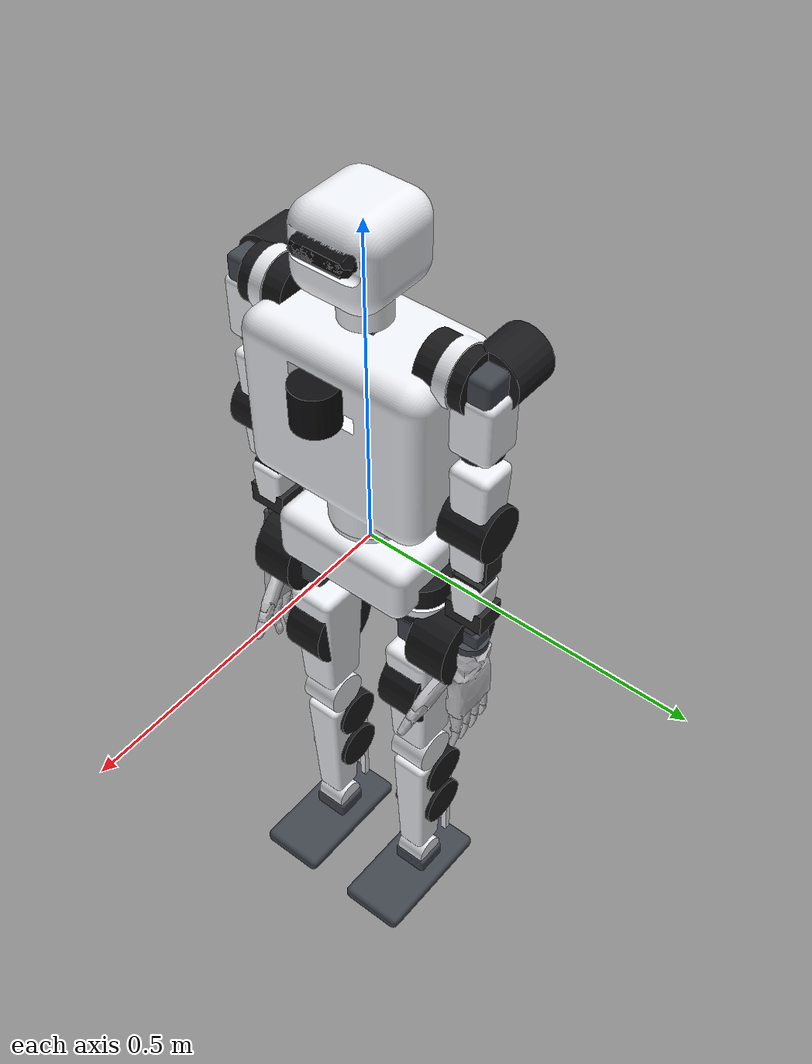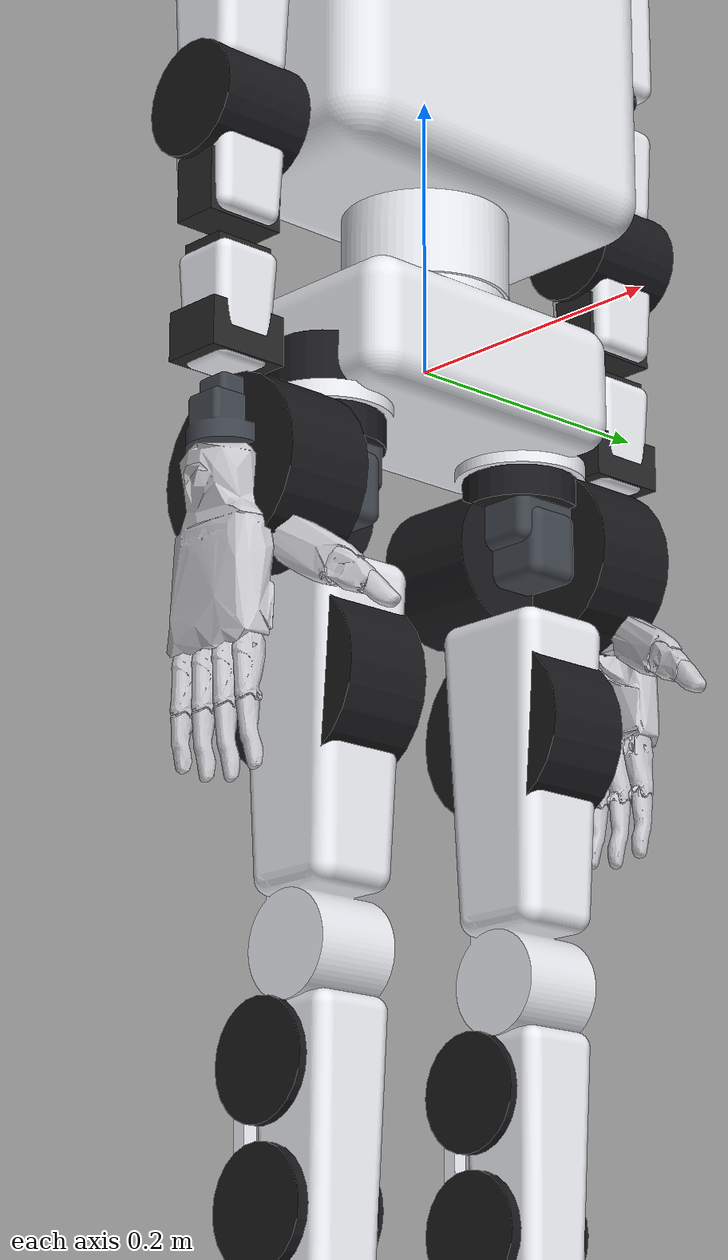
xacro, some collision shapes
<?xml version="1.0"?>
<!-- GENERATED by src/midibot_cad/scripts/generate_urdf.py - do not edit by hand -->
<robot name="midibot" xmlns:xacro="http://www.ros.org/wiki/xacro">
  <xacro:arg name="vendor_meshes" default="false"/>
  <!-- Dynamixel CAD must be downloaded by hand (see COMPONENTS.md), so it has its own switch -->
  <xacro:arg name="dxl_meshes" default="false"/>
  <xacro:arg name="sim" default="true"/>
  <xacro:arg name="sensors" default="true"/>
  <xacro:arg name="controllers_file" default=""/>
  <material name="shell"><color rgba="0.92 0.93 0.95 1"/></material>
  <material name="frame"><color rgba="0.25 0.27 0.30 1"/></material>
  <material name="actuator"><color rgba="0.10 0.10 0.11 1"/></material>
  <material name="dxl"><color rgba="0.15 0.15 0.15 1"/></material>
  <material name="sensor"><color rgba="0.05 0.05 0.06 1"/></material>
  <material name="accent"><color rgba="0.95 0.45 0.10 1"/></material>
  <material name="hand"><color rgba="0.80 0.80 0.82 1"/></material>
  <link name="base_link"/>
  <joint name="base_to_pelvis" type="fixed"><parent link="base_link"/><child link="pelvis"/><origin xyz="0 0 0" rpy="0 0 0"/></joint>
  <link name="pelvis">
    <inertial><origin xyz="-0.000823731 4.57334e-09 -0.0164109" rpy="0 0 0"/><mass value="4.85600"/><inertia ixx="2.4040e-02" ixy="-9.7713e-10" ixz="2.5648e-05" iyy="8.6649e-03" iyz="1.2006e-09" izz="2.3952e-02"/></inertial>
    <visual><origin xyz="0 0 0" rpy="0 0 0"/><geometry><mesh filename="package://midibot_description/meshes/structure/pelvis.stl"/></geometry><material name="shell"/></visual>
    <xacro:if value="$(arg vendor_meshes)"><visual><origin xyz="0 0 0.005" rpy="0.000000 -0.000000 0.000000"/><geometry><mesh filename="package://midibot_description/meshes/vendor/rmd_x8_p20_120.stl"/></geometry><material name="actuator"/></visual></xacro:if>
    <xacro:unless value="$(arg vendor_meshes)"><visual><origin xyz="0 0 0.005" rpy="0.000000 -0.000000 0.000000"/><geometry><cylinder radius="0.0500" length="0.0760"/></geometry><material name="actuator"/></visual></xacro:unless>
    <xacro:if value="$(arg vendor_meshes)"><visual><origin xyz="0 0.09 -0.045" rpy="0.000000 -0.000000 0.000000"/><geometry><mesh filename="package://midibot_description/meshes/vendor/rmd_x6_p20_60.stl"/></geometry><material name="actuator"/></visual></xacro:if>
    <xacro:unless value="$(arg vendor_meshes)"><visual><origin xyz="0 0.09 -0.045" rpy="0.000000 -0.000000 0.000000"/><geometry><cylinder radius="0.0400" length="0.0690"/></geometry><material name="actuator"/></visual></xacro:unless>
    <xacro:if value="$(arg vendor_meshes)"><visual><origin xyz="0 -0.09 -0.045" rpy="0.000000 -0.000000 0.000000"/><geometry><mesh filename="package://midibot_description/meshes/vendor/rmd_x6_p20_60.stl"/></geometry><material name="actuator"/></visual></xacro:if>
    <xacro:unless value="$(arg vendor_meshes)"><visual><origin xyz="0 -0.09 -0.045" rpy="0.000000 -0.000000 0.000000"/><geometry><cylinder radius="0.0400" length="0.0690"/></geometry><material name="actuator"/></visual></xacro:unless>
    <collision><origin xyz="0 0 -0.005" rpy="0 0 0"/><geometry><box size="0.1500 0.2200 0.0900"/></geometry></collision>
  </link>
  <link name="torso">
    <inertial><origin xyz="-0.00798314 3.89044e-08 0.165597" rpy="0 0 0"/><mass value="8.88700"/><inertia ixx="1.1102e-01" ixy="-1.8285e-09" ixz="-5.3976e-03" iyy="7.1881e-02" iyz="-3.1743e-08" izz="7.4068e-02"/></inertial>
    <visual><origin xyz="0 0 0" rpy="0 0 0"/><geometry><mesh filename="package://midibot_description/meshes/structure/torso.stl"/></geometry><material name="shell"/></visual>
    <xacro:if value="$(arg vendor_meshes)"><visual><origin xyz="0.095 0 0.215" rpy="0 0 0"/><geometry><mesh filename="package://midibot_description/meshes/vendor/livox_mid360.stl"/></geometry><material name="sensor"/></visual></xacro:if>
    <xacro:unless value="$(arg vendor_meshes)"><visual><origin xyz="0.095 0 0.215" rpy="0 0 0"/><geometry><cylinder radius="0.0325" length="0.060"/></geometry><material name="sensor"/></visual></xacro:unless>
    <xacro:if value="$(arg dxl_meshes)"><visual><origin xyz="0 0 0.29" rpy="0.000000 -0.000000 0.000000"/><geometry><mesh filename="package://midibot_description/meshes/vendor/dxl_xm430.stl"/></geometry><material name="dxl"/></visual></xacro:if>
    <xacro:unless value="$(arg dxl_meshes)"><visual><origin xyz="0 0 0.29" rpy="0.000000 -0.000000 0.000000"/><geometry><box size="0.0285 0.0465 0.0340"/></geometry><material name="dxl"/></visual></xacro:unless>
    <xacro:if value="$(arg vendor_meshes)"><visual><origin xyz="0 0.135 0.27" rpy="-1.570796 -0.000000 0.000000"/><geometry><mesh filename="package://midibot_description/meshes/vendor/rmd_x6_p20_60.stl"/></geometry><material name="actuator"/></visual></xacro:if>
    <xacro:unless value="$(arg vendor_meshes)"><visual><origin xyz="0 0.135 0.27" rpy="-1.570796 -0.000000 0.000000"/><geometry><cylinder radius="0.0400" length="0.0690"/></geometry><material name="actuator"/></visual></xacro:unless>
    <xacro:if value="$(arg vendor_meshes)"><visual><origin xyz="0 -0.135 0.27" rpy="-1.570796 -0.000000 0.000000"/><geometry><mesh filename="package://midibot_description/meshes/vendor/rmd_x6_p20_60.stl"/></geometry><material name="actuator"/></visual></xacro:if>
    <xacro:unless value="$(arg vendor_meshes)"><visual><origin xyz="0 -0.135 0.27" rpy="-1.570796 -0.000000 0.000000"/><geometry><cylinder radius="0.0400" length="0.0690"/></geometry><material name="actuator"/></visual></xacro:unless>
    <collision><origin xyz="0 0 0.15" rpy="0 0 0"/><geometry><box size="0.1700 0.2800 0.2500"/></geometry></collision>
  </link>
  <link name="left_hip_yaw_link">
    <inertial><origin xyz="-0.0406452 1.0027e-09 -0.0625806" rpy="0 0 0"/><mass value="1.55000"/><inertia ixx="1.8998e-03" ixy="-6.3170e-11" ixz="-1.5242e-04" iyy="1.9799e-03" iyz="-3.1196e-11" izz="1.9015e-03"/></inertial>
    <visual><origin xyz="0 0 0" rpy="0 0 0"/><geometry><mesh filename="package://midibot_description/meshes/structure/hip_yaw_link.stl"/></geometry><material name="frame"/></visual>
    <xacro:if value="$(arg vendor_meshes)"><visual><origin xyz="-0.045 0 -0.065" rpy="-0.000000 1.570796 0.000000"/><geometry><mesh filename="package://midibot_description/meshes/vendor/rmd_x8_p20_120.stl"/></geometry><material name="actuator"/></visual></xacro:if>
    <xacro:unless value="$(arg vendor_meshes)"><visual><origin xyz="-0.045 0 -0.065" rpy="-0.000000 1.570796 0.000000"/><geometry><cylinder radius="0.0500" length="0.0760"/></geometry><material name="actuator"/></visual></xacro:unless>
  </link>
  <link name="left_hip_roll_link">
    <inertial><origin xyz="1.16384e-19 0.0445652 -1.33698e-09" rpy="0 0 0"/><mass value="1.84000"/><inertia ixx="2.6366e-03" ixy="9.0416e-21" ixz="-9.2016e-22" iyy="3.2682e-03" iyz="-1.2197e-10" izz="2.6748e-03"/></inertial>
    <visual><origin xyz="0 0 0" rpy="0 0 0"/><geometry><mesh filename="package://midibot_description/meshes/structure/hip_roll_link.stl"/></geometry><material name="frame"/></visual>
    <xacro:if value="$(arg vendor_meshes)"><visual><origin xyz="0 0.05 0" rpy="-1.570796 -0.000000 0.000000"/><geometry><mesh filename="package://midibot_description/meshes/vendor/rmd_x10_p20_200.stl"/></geometry><material name="actuator"/></visual></xacro:if>
    <xacro:unless value="$(arg vendor_meshes)"><visual><origin xyz="0 0.05 0" rpy="-1.570796 -0.000000 0.000000"/><geometry><cylinder radius="0.0620" length="0.0635"/></geometry><material name="actuator"/></visual></xacro:unless>
  </link>
  <link name="left_thigh">
    <inertial><origin xyz="-0.000155737 -3.20059e-10 -0.144357" rpy="0 0 0"/><mass value="2.39000"/><inertia ixx="8.1582e-03" ixy="-2.2132e-10" ixz="-3.1148e-05" iyy="9.2937e-03" iyz="-1.4241e-11" izz="2.7797e-03"/></inertial>
    <visual><origin xyz="0 0 0" rpy="0 0 0"/><geometry><mesh filename="package://midibot_description/meshes/structure/thigh.stl"/></geometry><material name="shell"/></visual>
    <xacro:if value="$(arg vendor_meshes)"><visual><origin xyz="0 0 -0.13" rpy="-1.570796 -0.000000 0.000000"/><geometry><mesh filename="package://midibot_description/meshes/vendor/rmd_x10_p20_200.stl"/></geometry><material name="actuator"/></visual></xacro:if>
    <xacro:unless value="$(arg vendor_meshes)"><visual><origin xyz="0 0 -0.13" rpy="-1.570796 -0.000000 0.000000"/><geometry><cylinder radius="0.0620" length="0.0635"/></geometry><material name="actuator"/></visual></xacro:unless>
    <collision><origin xyz="0 0 -0.165" rpy="0 0 0"/><geometry><box size="0.0850 0.0720 0.2600"/></geometry></collision>
  </link>
  <link name="left_shank">
    <inertial><origin xyz="-0.0154775 -5.9063e-10 -0.125999" rpy="0 0 0"/><mass value="2.19000"/><inertia ixx="9.1635e-03" ixy="2.2488e-11" ixz="3.0158e-04" iyy="9.3662e-03" iyz="-1.4051e-10" izz="1.7733e-03"/></inertial>
    <visual><origin xyz="0 0 0" rpy="0 0 0"/><geometry><mesh filename="package://midibot_description/meshes/structure/shank.stl"/></geometry><material name="shell"/></visual>
    <xacro:if value="$(arg vendor_meshes)"><visual><origin xyz="-0.02 0 -0.07" rpy="-1.570796 -0.000000 0.000000"/><geometry><mesh filename="package://midibot_description/meshes/vendor/rmd_x6_p20_60.stl"/></geometry><material name="actuator"/></visual></xacro:if>
    <xacro:unless value="$(arg vendor_meshes)"><visual><origin xyz="-0.02 0 -0.07" rpy="-1.570796 -0.000000 0.000000"/><geometry><cylinder radius="0.0400" length="0.0690"/></geometry><material name="actuator"/></visual></xacro:unless>
    <xacro:if value="$(arg vendor_meshes)"><visual><origin xyz="-0.02 0 -0.16" rpy="-1.570796 -0.000000 0.000000"/><geometry><mesh filename="package://midibot_description/meshes/vendor/rmd_x6_p20_60.stl"/></geometry><material name="actuator"/></visual></xacro:if>
    <xacro:unless value="$(arg vendor_meshes)"><visual><origin xyz="-0.02 0 -0.16" rpy="-1.570796 -0.000000 0.000000"/><geometry><cylinder radius="0.0400" length="0.0690"/></geometry><material name="actuator"/></visual></xacro:unless>
    <collision><origin xyz="0 0 -0.15" rpy="0 0 0"/><geometry><box size="0.0650 0.0580 0.2500"/></geometry></collision>
  </link>
  <link name="left_ankle_pitch_link">
    <inertial><origin xyz="0 3.21677e-09 -3.21677e-09" rpy="0 0 0"/><mass value="0.08000"/><inertia ixx="1.3075e-05" ixy="3.4982e-23" ixz="9.6201e-23" iyy="1.3075e-05" iyz="-8.2766e-19" izz="1.3075e-05"/></inertial>
    <visual><origin xyz="0 0 0" rpy="0 0 0"/><geometry><mesh filename="package://midibot_description/meshes/structure/ankle_pitch_link.stl"/></geometry><material name="frame"/></visual>
  </link>
  <link name="left_foot">
    <inertial><origin xyz="0.0216374 6.72803e-09 -0.0439586" rpy="0 0 0"/><mass value="0.40000"/><inertia ixx="3.9630e-04" ixy="-1.3202e-12" ixz="3.0651e-05" iyy="1.4443e-03" iyz="1.0754e-10" izz="1.7351e-03"/></inertial>
    <visual><origin xyz="0 0 0" rpy="0 0 0"/><geometry><mesh filename="package://midibot_description/meshes/structure/foot.stl"/></geometry><material name="frame"/></visual>
    <collision><origin xyz="0.025 0 -0.0475" rpy="0 0 0"/><geometry><box size="0.2200 0.1100 0.0250"/></geometry></collision>
  </link>
  <link name="right_hip_yaw_link">
    <inertial><origin xyz="-0.0406452 1.0027e-09 -0.0625806" rpy="0 0 0"/><mass value="1.55000"/><inertia ixx="1.8998e-03" ixy="-6.3170e-11" ixz="-1.5242e-04" iyy="1.9799e-03" iyz="-3.1196e-11" izz="1.9015e-03"/></inertial>
    <visual><origin xyz="0 0 0" rpy="0 0 0"/><geometry><mesh filename="package://midibot_description/meshes/structure/hip_yaw_link.stl"/></geometry><material name="frame"/></visual>
    <xacro:if value="$(arg vendor_meshes)"><visual><origin xyz="-0.045 0 -0.065" rpy="-0.000000 1.570796 0.000000"/><geometry><mesh filename="package://midibot_description/meshes/vendor/rmd_x8_p20_120.stl"/></geometry><material name="actuator"/></visual></xacro:if>
    <xacro:unless value="$(arg vendor_meshes)"><visual><origin xyz="-0.045 0 -0.065" rpy="-0.000000 1.570796 0.000000"/><geometry><cylinder radius="0.0500" length="0.0760"/></geometry><material name="actuator"/></visual></xacro:unless>
  </link>
  <link name="right_hip_roll_link">
    <inertial><origin xyz="1.16384e-19 -0.0445652 -1.33698e-09" rpy="0 0 0"/><mass value="1.84000"/><inertia ixx="2.6366e-03" ixy="-1.0045e-20" ixz="-9.2016e-22" iyy="3.2682e-03" iyz="9.7296e-11" izz="2.6748e-03"/></inertial>
    <visual><origin xyz="0 0 0" rpy="0 0 0"/><geometry><mesh filename="package://midibot_description/meshes/structure/hip_roll_link.stl"/></geometry><material name="frame"/></visual>
    <xacro:if value="$(arg vendor_meshes)"><visual><origin xyz="0 -0.05 0" rpy="-1.570796 -0.000000 0.000000"/><geometry><mesh filename="package://midibot_description/meshes/vendor/rmd_x10_p20_200.stl"/></geometry><material name="actuator"/></visual></xacro:if>
    <xacro:unless value="$(arg vendor_meshes)"><visual><origin xyz="0 -0.05 0" rpy="-1.570796 -0.000000 0.000000"/><geometry><cylinder radius="0.0620" length="0.0635"/></geometry><material name="actuator"/></visual></xacro:unless>
  </link>
  <link name="right_thigh">
    <inertial><origin xyz="-0.000155737 -3.20059e-10 -0.144357" rpy="0 0 0"/><mass value="2.39000"/><inertia ixx="8.1582e-03" ixy="-2.2132e-10" ixz="-3.1148e-05" iyy="9.2937e-03" iyz="-1.4241e-11" izz="2.7797e-03"/></inertial>
    <visual><origin xyz="0 0 0" rpy="0 0 0"/><geometry><mesh filename="package://midibot_description/meshes/structure/thigh.stl"/></geometry><material name="shell"/></visual>
    <xacro:if value="$(arg vendor_meshes)"><visual><origin xyz="0 0 -0.13" rpy="-1.570796 -0.000000 0.000000"/><geometry><mesh filename="package://midibot_description/meshes/vendor/rmd_x10_p20_200.stl"/></geometry><material name="actuator"/></visual></xacro:if>
    <xacro:unless value="$(arg vendor_meshes)"><visual><origin xyz="0 0 -0.13" rpy="-1.570796 -0.000000 0.000000"/><geometry><cylinder radius="0.0620" length="0.0635"/></geometry><material name="actuator"/></visual></xacro:unless>
    <collision><origin xyz="0 0 -0.165" rpy="0 0 0"/><geometry><box size="0.0850 0.0720 0.2600"/></geometry></collision>
  </link>
  <link name="right_shank">
    <inertial><origin xyz="-0.0154775 -5.9063e-10 -0.125999" rpy="0 0 0"/><mass value="2.19000"/><inertia ixx="9.1635e-03" ixy="2.2488e-11" ixz="3.0158e-04" iyy="9.3662e-03" iyz="-1.4051e-10" izz="1.7733e-03"/></inertial>
    <visual><origin xyz="0 0 0" rpy="0 0 0"/><geometry><mesh filename="package://midibot_description/meshes/structure/shank.stl"/></geometry><material name="shell"/></visual>
    <xacro:if value="$(arg vendor_meshes)"><visual><origin xyz="-0.02 0 -0.07" rpy="-1.570796 -0.000000 0.000000"/><geometry><mesh filename="package://midibot_description/meshes/vendor/rmd_x6_p20_60.stl"/></geometry><material name="actuator"/></visual></xacro:if>
    <xacro:unless value="$(arg vendor_meshes)"><visual><origin xyz="-0.02 0 -0.07" rpy="-1.570796 -0.000000 0.000000"/><geometry><cylinder radius="0.0400" length="0.0690"/></geometry><material name="actuator"/></visual></xacro:unless>
    <xacro:if value="$(arg vendor_meshes)"><visual><origin xyz="-0.02 0 -0.16" rpy="-1.570796 -0.000000 0.000000"/><geometry><mesh filename="package://midibot_description/meshes/vendor/rmd_x6_p20_60.stl"/></geometry><material name="actuator"/></visual></xacro:if>
    <xacro:unless value="$(arg vendor_meshes)"><visual><origin xyz="-0.02 0 -0.16" rpy="-1.570796 -0.000000 0.000000"/><geometry><cylinder radius="0.0400" length="0.0690"/></geometry><material name="actuator"/></visual></xacro:unless>
    <collision><origin xyz="0 0 -0.15" rpy="0 0 0"/><geometry><box size="0.0650 0.0580 0.2500"/></geometry></collision>
  </link>
  <link name="right_ankle_pitch_link">
    <inertial><origin xyz="0 3.21677e-09 -3.21677e-09" rpy="0 0 0"/><mass value="0.08000"/><inertia ixx="1.3075e-05" ixy="3.4982e-23" ixz="9.6201e-23" iyy="1.3075e-05" iyz="-8.2766e-19" izz="1.3075e-05"/></inertial>
    <visual><origin xyz="0 0 0" rpy="0 0 0"/><geometry><mesh filename="package://midibot_description/meshes/structure/ankle_pitch_link.stl"/></geometry><material name="frame"/></visual>
  </link>
  <link name="right_foot">
    <inertial><origin xyz="0.0216374 6.72803e-09 -0.0439586" rpy="0 0 0"/><mass value="0.40000"/><inertia ixx="3.9630e-04" ixy="-1.3202e-12" ixz="3.0651e-05" iyy="1.4443e-03" iyz="1.0754e-10" izz="1.7351e-03"/></inertial>
    <visual><origin xyz="0 0 0" rpy="0 0 0"/><geometry><mesh filename="package://midibot_description/meshes/structure/foot.stl"/></geometry><material name="frame"/></visual>
    <collision><origin xyz="0.025 0 -0.0475" rpy="0 0 0"/><geometry><box size="0.2200 0.1100 0.0250"/></geometry></collision>
  </link>
  <link name="left_shoulder_pitch_link">
    <inertial><origin xyz="-0.0392553 1.44728e-09 -1.44816e-09" rpy="0 0 0"/><mass value="0.94000"/><inertia ixx="7.0800e-04" ixy="-5.3405e-11" ixz="5.3437e-11" iyy="9.2231e-04" iyz="-3.3926e-12" izz="9.1732e-04"/></inertial>
    <visual><origin xyz="0 0 0" rpy="0 0 0"/><geometry><mesh filename="package://midibot_description/meshes/structure/shoulder_pitch_link.stl"/></geometry><material name="frame"/></visual>
    <xacro:if value="$(arg vendor_meshes)"><visual><origin xyz="-0.045 0 0" rpy="-0.000000 1.570796 0.000000"/><geometry><mesh filename="package://midibot_description/meshes/vendor/rmd_x6_p20_60.stl"/></geometry><material name="actuator"/></visual></xacro:if>
    <xacro:unless value="$(arg vendor_meshes)"><visual><origin xyz="-0.045 0 0" rpy="-0.000000 1.570796 0.000000"/><geometry><cylinder radius="0.0400" length="0.0690"/></geometry><material name="actuator"/></visual></xacro:unless>
  </link>
  <link name="left_shoulder_roll_link">
    <inertial><origin xyz="0 4.93672e-09 -0.0588525" rpy="0 0 0"/><mass value="0.61000"/><inertia ixx="4.6786e-04" ixy="5.0311e-22" ixz="0.0000e+00" iyy="4.6786e-04" iyz="-6.8799e-11" izz="3.0246e-04"/></inertial>
    <visual><origin xyz="0 0 0" rpy="0 0 0"/><geometry><mesh filename="package://midibot_description/meshes/structure/shoulder_roll_link.stl"/></geometry><material name="shell"/></visual>
    <xacro:if value="$(arg vendor_meshes)"><visual><origin xyz="0 0 -0.065" rpy="0.000000 -0.000000 0.000000"/><geometry><mesh filename="package://midibot_description/meshes/vendor/rmd_x4_p36_36.stl"/></geometry><material name="actuator"/></visual></xacro:if>
    <xacro:unless value="$(arg vendor_meshes)"><visual><origin xyz="0 0 -0.065" rpy="0.000000 -0.000000 0.000000"/><geometry><cylinder radius="0.0290" length="0.0640"/></geometry><material name="actuator"/></visual></xacro:unless>
    <collision><origin xyz="0 0 -0.05" rpy="0 0 0"/><geometry><box size="0.0620 0.0620 0.0900"/></geometry></collision>
  </link>
  <link name="left_shoulder_yaw_link">
    <inertial><origin xyz="-4.73471e-08 6.74665e-10 -0.110775" rpy="0 0 0"/><mass value="1.07000"/><inertia ixx="1.3451e-03" ixy="-4.1958e-11" ixz="8.4380e-10" iyy="1.3374e-03" iyz="-1.9696e-11" izz="7.7999e-04"/></inertial>
    <visual><origin xyz="0 0 0" rpy="0 0 0"/><geometry><mesh filename="package://midibot_description/meshes/structure/shoulder_yaw_link.stl"/></geometry><material name="shell"/></visual>
    <xacro:if value="$(arg vendor_meshes)"><visual><origin xyz="0 0 -0.12" rpy="-1.570796 -0.000000 0.000000"/><geometry><mesh filename="package://midibot_description/meshes/vendor/rmd_x6_p20_60.stl"/></geometry><material name="actuator"/></visual></xacro:if>
    <xacro:unless value="$(arg vendor_meshes)"><visual><origin xyz="0 0 -0.12" rpy="-1.570796 -0.000000 0.000000"/><geometry><cylinder radius="0.0400" length="0.0690"/></geometry><material name="actuator"/></visual></xacro:unless>
    <collision><origin xyz="0 0 -0.055" rpy="0 0 0"/><geometry><box size="0.0580 0.0580 0.1000"/></geometry></collision>
  </link>
  <link name="left_elbow_link">
    <inertial><origin xyz="-5.58957e-09 9.06133e-10 -0.0548244" rpy="0 0 0"/><mass value="0.31500"/><inertia ixx="1.5804e-04" ixy="-2.5528e-11" ixz="4.7641e-14" iyy="1.2642e-04" iyz="5.9390e-12" izz="1.2770e-04"/></inertial>
    <visual><origin xyz="0 0 0" rpy="0 0 0"/><geometry><mesh filename="package://midibot_description/meshes/structure/elbow_link.stl"/></geometry><material name="shell"/></visual>
    <xacro:if value="$(arg dxl_meshes)"><visual><origin xyz="0 0 -0.06" rpy="0.000000 -0.000000 0.000000"/><geometry><mesh filename="package://midibot_description/meshes/vendor/dxl_xh540.stl"/></geometry><material name="dxl"/></visual></xacro:if>
    <xacro:unless value="$(arg dxl_meshes)"><visual><origin xyz="0 0 -0.06" rpy="0.000000 -0.000000 0.000000"/><geometry><box size="0.0335 0.0585 0.0440"/></geometry><material name="dxl"/></visual></xacro:unless>
    <collision><origin xyz="0 0 -0.04" rpy="0 0 0"/><geometry><box size="0.0520 0.0520 0.0900"/></geometry></collision>
  </link>
  <link name="left_wrist_yaw_link">
    <inertial><origin xyz="-3.52638e-09 5.19735e-10 -0.0510253" rpy="0 0 0"/><mass value="0.48000"/><inertia ixx="3.4024e-04" ixy="-2.2135e-11" ixz="3.6367e-13" iyy="3.0861e-04" iyz="1.8143e-11" izz="1.6599e-04"/></inertial>
    <visual><origin xyz="0 0 0" rpy="0 0 0"/><geometry><mesh filename="package://midibot_description/meshes/structure/wrist_yaw_link.stl"/></geometry><material name="shell"/></visual>
    <xacro:if value="$(arg dxl_meshes)"><visual><origin xyz="0 0 -0.035" rpy="-1.570796 -0.000000 0.000000"/><geometry><mesh filename="package://midibot_description/meshes/vendor/dxl_xh540.stl"/></geometry><material name="dxl"/></visual></xacro:if>
    <xacro:unless value="$(arg dxl_meshes)"><visual><origin xyz="0 0 -0.035" rpy="-1.570796 -0.000000 0.000000"/><geometry><box size="0.0335 0.0585 0.0440"/></geometry><material name="dxl"/></visual></xacro:unless>
    <xacro:if value="$(arg dxl_meshes)"><visual><origin xyz="0 0 -0.07" rpy="-0.000000 1.570796 0.000000"/><geometry><mesh filename="package://midibot_description/meshes/vendor/dxl_xh540.stl"/></geometry><material name="dxl"/></visual></xacro:if>
    <xacro:unless value="$(arg dxl_meshes)"><visual><origin xyz="0 0 -0.07" rpy="-0.000000 1.570796 0.000000"/><geometry><box size="0.0335 0.0585 0.0440"/></geometry><material name="dxl"/></visual></xacro:unless>
    <collision><origin xyz="0 0 -0.05" rpy="0 0 0"/><geometry><box size="0.0460 0.0460 0.0900"/></geometry></collision>
  </link>
  <link name="left_wrist_pitch_link">
    <inertial><origin xyz="1.06404e-18 6.11523e-09 -6.11523e-09" rpy="0 0 0"/><mass value="0.03000"/><inertia ixx="3.1737e-06" ixy="-6.2344e-24" ixz="-1.4028e-23" iyy="3.1737e-06" iyz="-1.1219e-18" izz="3.1737e-06"/></inertial>
    <visual><origin xyz="0 0 0" rpy="0 0 0"/><geometry><mesh filename="package://midibot_description/meshes/structure/wrist_pitch_link.stl"/></geometry><material name="frame"/></visual>
  </link>
  <link name="left_wrist_roll_link">
    <inertial><origin xyz="1.33763e-10 1.99223e-09 -0.0195322" rpy="0 0 0"/><mass value="0.06000"/><inertia ixx="1.4882e-05" ixy="1.6014e-20" ixz="7.5987e-14" iyy="1.3055e-05" iyz="-1.9088e-15" izz="1.5141e-05"/></inertial>
    <visual><origin xyz="0 0 0" rpy="0 0 0"/><geometry><mesh filename="package://midibot_description/meshes/structure/wrist_roll_link.stl"/></geometry><material name="frame"/></visual>
  </link>
  <link name="L_hand_base_link">
    <inertial><origin xyz="-0.002551 -0.066047 -0.0019357" rpy="0 0 0"/><mass value="0.48963"/><inertia ixx="3.2340e-04" ixy="2.1995e-06" ixz="-1.7694e-06" iyy="2.8384e-04" iyz="1.5968e-06" izz="2.7723e-04"/></inertial>
    <visual><origin xyz="0 0 0" rpy="0 0 0"/><geometry><mesh filename="package://midibot_description/meshes/hands/L_hand_base_link.stl"/></geometry><material name="hand"/></visual>
    <collision><origin xyz="-0.000642858 -0.0709727 -0.00204488" rpy="0 0 0"/><geometry><box size="0.0501 0.1278 0.0737"/></geometry></collision>
  </link>
  <link name="L_thumb_proximal_base">
    <inertial><origin xyz="0.0048817 0.00038782 -0.00722" rpy="0 0 0"/><mass value="0.00189"/><inertia ixx="5.5158e-08" ixy="-1.1803e-08" ixz="-4.6743e-09" iyy="8.2164e-08" iyz="-1.3521e-09" izz="6.7434e-08"/></inertial>
    <visual><origin xyz="0 0 0" rpy="0 0 0"/><geometry><mesh filename="package://midibot_description/meshes/hands/Link11_L.stl"/></geometry><material name="hand"/></visual>
    <collision><origin xyz="0.00420149 -0.000629605 -0.00548027" rpy="0 0 0"/><geometry><box size="0.0181 0.0131 0.0143"/></geometry></collision>
  </link>
  <link name="L_thumb_proximal">
    <inertial><origin xyz="0.021936 -0.01279 -0.0080386" rpy="0 0 0"/><mass value="0.00661"/><inertia ixx="1.5693e-06" ixy="7.8339e-07" ixz="8.5959e-10" iyy="1.7356e-06" iyz="1.0378e-09" izz="2.7870e-06"/></inertial>
    <visual><origin xyz="0 0 0" rpy="0 0 0"/><geometry><mesh filename="package://midibot_description/meshes/hands/Link12_L.stl"/></geometry><material name="hand"/></visual>
    <collision><origin xyz="0.0278775 -0.0137507 -0.00781538" rpy="0 0 0"/><geometry><box size="0.0539 0.0431 0.0162"/></geometry></collision>
  </link>
  <link name="L_thumb_intermediate">
    <inertial><origin xyz="0.0095531 0.0016282 -0.0072002" rpy="0 0 0"/><mass value="0.00378"/><inertia ixx="3.6981e-07" ixy="9.8603e-08" ixz="-2.8173e-12" iyy="3.2395e-07" iyz="-2.8028e-12" izz="4.6532e-07"/></inertial>
    <visual><origin xyz="0 0 0" rpy="0 0 0"/><geometry><mesh filename="package://midibot_description/meshes/hands/Link13_L.stl"/></geometry><material name="hand"/></visual>
    <collision><origin xyz="0.00663063 0.00122298 -0.00723001" rpy="0 0 0"/><geometry><box size="0.0322 0.0267 0.0141"/></geometry></collision>
  </link>
  <link name="L_thumb_distal">
    <inertial><origin xyz="0.0092888 -0.004953 -0.0060033" rpy="0 0 0"/><mass value="0.00334"/><inertia ixx="1.3632e-07" ixy="5.6787e-08" ixz="-9.1939e-11" iyy="1.4052e-07" iyz="1.2145e-10" izz="2.0026e-07"/></inertial>
    <visual><origin xyz="0 0 0" rpy="0 0 0"/><geometry><mesh filename="package://midibot_description/meshes/hands/Link14_L.stl"/></geometry><material name="hand"/></visual>
    <collision><origin xyz="0.00855278 -0.0033945 -0.00599715" rpy="0 0 0"/><geometry><box size="0.0233 0.0208 0.0125"/></geometry></collision>
  </link>
  <link name="L_index_proximal">
    <inertial><origin xyz="0.0012971 -0.011934 -0.0059998" rpy="0 0 0"/><mass value="0.00424"/><inertia ixx="6.6215e-07" ixy="1.8442e-08" ixz="1.3746e-12" iyy="2.1167e-07" iyz="-1.4773e-11" izz="6.9402e-07"/></inertial>
    <visual><origin xyz="0 0 0" rpy="0 0 0"/><geometry><mesh filename="package://midibot_description/meshes/hands/Link15_L.stl"/></geometry><material name="hand"/></visual>
    <collision><origin xyz="0.000658989 -0.0130309 -0.00597555" rpy="0 0 0"/><geometry><box size="0.0182 0.0389 0.0123"/></geometry></collision>
  </link>
  <link name="L_index_intermediate">
    <inertial><origin xyz="0.0021753 -0.019567 -0.005" rpy="0 0 0"/><mass value="0.00457"/><inertia ixx="7.6284e-07" ixy="-8.0630e-08" ixz="3.6797e-13" iyy="9.4308e-08" iyz="1.5743e-13" izz="7.8176e-07"/></inertial>
    <visual><origin xyz="0 0 0" rpy="0 0 0"/><geometry><mesh filename="package://midibot_description/meshes/hands/Link16_L.stl"/></geometry><material name="hand"/></visual>
    <collision><origin xyz="0.00277799 -0.0186311 -0.00501963" rpy="0 0 0"/><geometry><box size="0.0140 0.0453 0.0107"/></geometry></collision>
  </link>
  <link name="L_middle_proximal">
    <inertial><origin xyz="0.0012971 -0.011934 -0.0059999" rpy="0 0 0"/><mass value="0.00424"/><inertia ixx="6.6215e-07" ixy="1.8442e-08" ixz="1.2299e-12" iyy="2.1167e-07" iyz="-1.4484e-11" izz="6.9402e-07"/></inertial>
    <visual><origin xyz="0 0 0" rpy="0 0 0"/><geometry><mesh filename="package://midibot_description/meshes/hands/Link17_L.stl"/></geometry><material name="hand"/></visual>
    <collision><origin xyz="0.000658989 -0.0130309 -0.00597555" rpy="0 0 0"/><geometry><box size="0.0182 0.0389 0.0123"/></geometry></collision>
  </link>
  <link name="L_middle_intermediate">
    <inertial><origin xyz="0.001921 -0.020796 -0.0049999" rpy="0 0 0"/><mass value="0.00504"/><inertia ixx="9.5823e-07" ixy="-1.1425e-07" ixz="-2.4186e-12" iyy="1.0646e-07" iyz="3.6974e-12" izz="9.8385e-07"/></inertial>
    <visual><origin xyz="0 0 0" rpy="0 0 0"/><geometry><mesh filename="package://midibot_description/meshes/hands/Link18_L.stl"/></geometry><material name="hand"/></visual>
    <collision><origin xyz="0.00245034 -0.0204521 -0.00499842" rpy="0 0 0"/><geometry><box size="0.0145 0.0480 0.0107"/></geometry></collision>
  </link>
  <link name="L_ring_proximal">
    <inertial><origin xyz="0.0012971 -0.011934 -0.0059999" rpy="0 0 0"/><mass value="0.00424"/><inertia ixx="6.6215e-07" ixy="1.8442e-08" ixz="9.6052e-13" iyy="2.1167e-07" iyz="-1.4124e-11" izz="6.9402e-07"/></inertial>
    <visual><origin xyz="0 0 0" rpy="0 0 0"/><geometry><mesh filename="package://midibot_description/meshes/hands/Link19_L.stl"/></geometry><material name="hand"/></visual>
    <collision><origin xyz="0.000658989 -0.0130309 -0.00597555" rpy="0 0 0"/><geometry><box size="0.0182 0.0389 0.0123"/></geometry></collision>
  </link>
  <link name="L_ring_intermediate">
    <inertial><origin xyz="0.0021753 -0.019567 -0.005" rpy="0 0 0"/><mass value="0.00457"/><inertia ixx="7.6285e-07" ixy="-8.0631e-08" ixz="3.3472e-14" iyy="9.4308e-08" iyz="-4.4773e-13" izz="7.8176e-07"/></inertial>
    <visual><origin xyz="0 0 0" rpy="0 0 0"/><geometry><mesh filename="package://midibot_description/meshes/hands/Link20_L.stl"/></geometry><material name="hand"/></visual>
    <collision><origin xyz="0.00275961 -0.0186311 -0.00500322" rpy="0 0 0"/><geometry><box size="0.0140 0.0453 0.0107"/></geometry></collision>
  </link>
  <link name="L_pinky_proximal">
    <inertial><origin xyz="0.0012971 -0.011934 -0.0059999" rpy="0 0 0"/><mass value="0.00424"/><inertia ixx="6.6215e-07" ixy="1.8442e-08" ixz="1.0279e-12" iyy="2.1167e-07" iyz="-1.4277e-11" izz="6.9402e-07"/></inertial>
    <visual><origin xyz="0 0 0" rpy="0 0 0"/><geometry><mesh filename="package://midibot_description/meshes/hands/Link21_L.stl"/></geometry><material name="hand"/></visual>
    <collision><origin xyz="0.000658989 -0.0130309 -0.00597555" rpy="0 0 0"/><geometry><box size="0.0182 0.0389 0.0123"/></geometry></collision>
  </link>
  <link name="L_pinky_intermediate">
    <inertial><origin xyz="0.0024788 -0.016208 -0.0050001" rpy="0 0 0"/><mass value="0.00360"/><inertia ixx="4.3923e-07" ixy="-4.1355e-08" ixz="1.2263e-12" iyy="7.0315e-08" iyz="3.1311e-12" izz="4.4881e-07"/></inertial>
    <visual><origin xyz="0 0 0" rpy="0 0 0"/><geometry><mesh filename="package://midibot_description/meshes/hands/Link22_L.stl"/></geometry><material name="hand"/></visual>
    <collision><origin xyz="0.00306693 -0.0148874 -0.00502469" rpy="0 0 0"/><geometry><box size="0.0131 0.0384 0.0108"/></geometry></collision>
  </link>
  <link name="right_shoulder_pitch_link">
    <inertial><origin xyz="-0.0392553 1.44728e-09 -1.44816e-09" rpy="0 0 0"/><mass value="0.94000"/><inertia ixx="7.0800e-04" ixy="-5.3405e-11" ixz="5.3437e-11" iyy="9.2231e-04" iyz="-3.3926e-12" izz="9.1732e-04"/></inertial>
    <visual><origin xyz="0 0 0" rpy="0 0 0"/><geometry><mesh filename="package://midibot_description/meshes/structure/shoulder_pitch_link.stl"/></geometry><material name="frame"/></visual>
    <xacro:if value="$(arg vendor_meshes)"><visual><origin xyz="-0.045 0 0" rpy="-0.000000 1.570796 0.000000"/><geometry><mesh filename="package://midibot_description/meshes/vendor/rmd_x6_p20_60.stl"/></geometry><material name="actuator"/></visual></xacro:if>
    <xacro:unless value="$(arg vendor_meshes)"><visual><origin xyz="-0.045 0 0" rpy="-0.000000 1.570796 0.000000"/><geometry><cylinder radius="0.0400" length="0.0690"/></geometry><material name="actuator"/></visual></xacro:unless>
  </link>
  <link name="right_shoulder_roll_link">
    <inertial><origin xyz="0 4.93672e-09 -0.0588525" rpy="0 0 0"/><mass value="0.61000"/><inertia ixx="4.6786e-04" ixy="5.0311e-22" ixz="0.0000e+00" iyy="4.6786e-04" iyz="-6.8799e-11" izz="3.0246e-04"/></inertial>
    <visual><origin xyz="0 0 0" rpy="0 0 0"/><geometry><mesh filename="package://midibot_description/meshes/structure/shoulder_roll_link.stl"/></geometry><material name="shell"/></visual>
    <xacro:if value="$(arg vendor_meshes)"><visual><origin xyz="0 0 -0.065" rpy="0.000000 -0.000000 0.000000"/><geometry><mesh filename="package://midibot_description/meshes/vendor/rmd_x4_p36_36.stl"/></geometry><material name="actuator"/></visual></xacro:if>
    <xacro:unless value="$(arg vendor_meshes)"><visual><origin xyz="0 0 -0.065" rpy="0.000000 -0.000000 0.000000"/><geometry><cylinder radius="0.0290" length="0.0640"/></geometry><material name="actuator"/></visual></xacro:unless>
    <collision><origin xyz="0 0 -0.05" rpy="0 0 0"/><geometry><box size="0.0620 0.0620 0.0900"/></geometry></collision>
  </link>
  <link name="right_shoulder_yaw_link">
    <inertial><origin xyz="-4.73471e-08 6.74665e-10 -0.110775" rpy="0 0 0"/><mass value="1.07000"/><inertia ixx="1.3451e-03" ixy="-4.1958e-11" ixz="8.4380e-10" iyy="1.3374e-03" iyz="-1.9696e-11" izz="7.7999e-04"/></inertial>
    <visual><origin xyz="0 0 0" rpy="0 0 0"/><geometry><mesh filename="package://midibot_description/meshes/structure/shoulder_yaw_link.stl"/></geometry><material name="shell"/></visual>
    <xacro:if value="$(arg vendor_meshes)"><visual><origin xyz="0 0 -0.12" rpy="-1.570796 -0.000000 0.000000"/><geometry><mesh filename="package://midibot_description/meshes/vendor/rmd_x6_p20_60.stl"/></geometry><material name="actuator"/></visual></xacro:if>
    <xacro:unless value="$(arg vendor_meshes)"><visual><origin xyz="0 0 -0.12" rpy="-1.570796 -0.000000 0.000000"/><geometry><cylinder radius="0.0400" length="0.0690"/></geometry><material name="actuator"/></visual></xacro:unless>
    <collision><origin xyz="0 0 -0.055" rpy="0 0 0"/><geometry><box size="0.0580 0.0580 0.1000"/></geometry></collision>
  </link>
  <link name="right_elbow_link">
    <inertial><origin xyz="-5.58957e-09 9.06133e-10 -0.0548244" rpy="0 0 0"/><mass value="0.31500"/><inertia ixx="1.5804e-04" ixy="-2.5528e-11" ixz="4.7641e-14" iyy="1.2642e-04" iyz="5.9390e-12" izz="1.2770e-04"/></inertial>
    <visual><origin xyz="0 0 0" rpy="0 0 0"/><geometry><mesh filename="package://midibot_description/meshes/structure/elbow_link.stl"/></geometry><material name="shell"/></visual>
    <xacro:if value="$(arg dxl_meshes)"><visual><origin xyz="0 0 -0.06" rpy="0.000000 -0.000000 0.000000"/><geometry><mesh filename="package://midibot_description/meshes/vendor/dxl_xh540.stl"/></geometry><material name="dxl"/></visual></xacro:if>
    <xacro:unless value="$(arg dxl_meshes)"><visual><origin xyz="0 0 -0.06" rpy="0.000000 -0.000000 0.000000"/><geometry><box size="0.0335 0.0585 0.0440"/></geometry><material name="dxl"/></visual></xacro:unless>
    <collision><origin xyz="0 0 -0.04" rpy="0 0 0"/><geometry><box size="0.0520 0.0520 0.0900"/></geometry></collision>
  </link>
  <link name="right_wrist_yaw_link">
    <inertial><origin xyz="-3.52638e-09 5.19735e-10 -0.0510253" rpy="0 0 0"/><mass value="0.48000"/><inertia ixx="3.4024e-04" ixy="-2.2135e-11" ixz="3.6367e-13" iyy="3.0861e-04" iyz="1.8143e-11" izz="1.6599e-04"/></inertial>
    <visual><origin xyz="0 0 0" rpy="0 0 0"/><geometry><mesh filename="package://midibot_description/meshes/structure/wrist_yaw_link.stl"/></geometry><material name="shell"/></visual>
    <xacro:if value="$(arg dxl_meshes)"><visual><origin xyz="0 0 -0.035" rpy="-1.570796 -0.000000 0.000000"/><geometry><mesh filename="package://midibot_description/meshes/vendor/dxl_xh540.stl"/></geometry><material name="dxl"/></visual></xacro:if>
    <xacro:unless value="$(arg dxl_meshes)"><visual><origin xyz="0 0 -0.035" rpy="-1.570796 -0.000000 0.000000"/><geometry><box size="0.0335 0.0585 0.0440"/></geometry><material name="dxl"/></visual></xacro:unless>
    <xacro:if value="$(arg dxl_meshes)"><visual><origin xyz="0 0 -0.07" rpy="-0.000000 1.570796 0.000000"/><geometry><mesh filename="package://midibot_description/meshes/vendor/dxl_xh540.stl"/></geometry><material name="dxl"/></visual></xacro:if>
    <xacro:unless value="$(arg dxl_meshes)"><visual><origin xyz="0 0 -0.07" rpy="-0.000000 1.570796 0.000000"/><geometry><box size="0.0335 0.0585 0.0440"/></geometry><material name="dxl"/></visual></xacro:unless>
    <collision><origin xyz="0 0 -0.05" rpy="0 0 0"/><geometry><box size="0.0460 0.0460 0.0900"/></geometry></collision>
  </link>
  <link name="right_wrist_pitch_link">
    <inertial><origin xyz="1.06404e-18 6.11523e-09 -6.11523e-09" rpy="0 0 0"/><mass value="0.03000"/><inertia ixx="3.1737e-06" ixy="-6.2344e-24" ixz="-1.4028e-23" iyy="3.1737e-06" iyz="-1.1219e-18" izz="3.1737e-06"/></inertial>
    <visual><origin xyz="0 0 0" rpy="0 0 0"/><geometry><mesh filename="package://midibot_description/meshes/structure/wrist_pitch_link.stl"/></geometry><material name="frame"/></visual>
  </link>
  <link name="right_wrist_roll_link">
    <inertial><origin xyz="1.33763e-10 1.99223e-09 -0.0195322" rpy="0 0 0"/><mass value="0.06000"/><inertia ixx="1.4882e-05" ixy="1.6014e-20" ixz="7.5987e-14" iyy="1.3055e-05" iyz="-1.9088e-15" izz="1.5141e-05"/></inertial>
    <visual><origin xyz="0 0 0" rpy="0 0 0"/><geometry><mesh filename="package://midibot_description/meshes/structure/wrist_roll_link.stl"/></geometry><material name="frame"/></visual>
  </link>
  <link name="R_hand_base_link">
    <inertial><origin xyz="-0.0025264 -0.066047 0.0019598" rpy="0 0 0"/><mass value="0.48964"/><inertia ixx="3.2281e-04" ixy="2.1711e-06" ixz="1.7709e-06" iyy="2.8383e-04" iyz="-1.6551e-06" izz="2.7666e-04"/></inertial>
    <visual><origin xyz="0 0 0" rpy="0 0 0"/><geometry><mesh filename="package://midibot_description/meshes/hands/R_hand_base_link.stl"/></geometry><material name="hand"/></visual>
    <collision><origin xyz="-0.00108727 -0.0706149 0.00177897" rpy="0 0 0"/><geometry><box size="0.0510 0.1269 0.0732"/></geometry></collision>
  </link>
  <link name="R_thumb_proximal_base">
    <inertial><origin xyz="-0.0048064 0.0009382 -0.00757" rpy="0 0 0"/><mass value="0.00189"/><inertia ixx="5.8160e-08" ixy="1.4539e-08" ixz="4.4910e-09" iyy="7.9161e-08" iyz="-1.8727e-09" izz="6.7433e-08"/></inertial>
    <visual><origin xyz="0 0 0" rpy="0 0 0"/><geometry><mesh filename="package://midibot_description/meshes/hands/Link11_R.stl"/></geometry><material name="hand"/></visual>
    <collision><origin xyz="-0.00443895 -6.91377e-05 -0.00583027" rpy="0 0 0"/><geometry><box size="0.0180 0.0146 0.0143"/></geometry></collision>
  </link>
  <link name="R_thumb_proximal">
    <inertial><origin xyz="0.021932 0.012785 -0.0080386" rpy="0 0 0"/><mass value="0.00661"/><inertia ixx="1.5686e-06" ixy="-7.8296e-07" ixz="8.9143e-10" iyy="1.7353e-06" iyz="-1.0191e-09" izz="2.7860e-06"/></inertial>
    <visual><origin xyz="0 0 0" rpy="0 0 0"/><geometry><mesh filename="package://midibot_description/meshes/hands/Link12_R.stl"/></geometry><material name="hand"/></visual>
    <collision><origin xyz="0.0278724 0.013995 -0.00820967" rpy="0 0 0"/><geometry><box size="0.0543 0.0428 0.0163"/></geometry></collision>
  </link>
  <link name="R_thumb_intermediate">
    <inertial><origin xyz="0.0095544 -0.0016282 -0.0071997" rpy="0 0 0"/><mass value="0.00378"/><inertia ixx="3.6981e-07" ixy="-9.8581e-08" ixz="-4.7469e-12" iyy="3.2394e-07" iyz="1.0939e-12" izz="4.6531e-07"/></inertial>
    <visual><origin xyz="0 0 0" rpy="0 0 0"/><geometry><mesh filename="package://midibot_description/meshes/hands/Link13_R.stl"/></geometry><material name="hand"/></visual>
    <collision><origin xyz="0.00650019 -0.00115247 -0.00707655" rpy="0 0 0"/><geometry><box size="0.0319 0.0267 0.0143"/></geometry></collision>
  </link>
  <link name="R_thumb_distal">
    <inertial><origin xyz="0.0092888 0.0049529 -0.0060033" rpy="0 0 0"/><mass value="0.00334"/><inertia ixx="1.3632e-07" ixy="-5.6788e-08" ixz="-9.2764e-11" iyy="1.4052e-07" iyz="-1.2283e-10" izz="2.0026e-07"/></inertial>
    <visual><origin xyz="0 0 0" rpy="0 0 0"/><geometry><mesh filename="package://midibot_description/meshes/hands/Link14_R.stl"/></geometry><material name="hand"/></visual>
    <collision><origin xyz="0.00860759 0.00340934 -0.00599295" rpy="0 0 0"/><geometry><box size="0.0232 0.0207 0.0125"/></geometry></collision>
  </link>
  <link name="R_index_proximal">
    <inertial><origin xyz="0.0012259 0.011942 -0.0060001" rpy="0 0 0"/><mass value="0.00424"/><inertia ixx="6.6232e-07" ixy="-1.5775e-08" ixz="1.8515e-12" iyy="2.1146e-07" iyz="-5.0828e-12" izz="6.9398e-07"/></inertial>
    <visual><origin xyz="0 0 0" rpy="0 0 0"/><geometry><mesh filename="package://midibot_description/meshes/hands/Link15_R.stl"/></geometry><material name="hand"/></visual>
    <collision><origin xyz="0.000643287 0.013012 -0.00602229" rpy="0 0 0"/><geometry><box size="0.0184 0.0387 0.0123"/></geometry></collision>
  </link>
  <link name="R_index_intermediate">
    <inertial><origin xyz="0.0019697 0.019589 -0.005" rpy="0 0 0"/><mass value="0.00457"/><inertia ixx="7.6111e-07" ixy="8.7637e-08" ixz="-3.7751e-13" iyy="9.6076e-08" iyz="9.9444e-13" izz="7.8179e-07"/></inertial>
    <visual><origin xyz="0 0 0" rpy="0 0 0"/><geometry><mesh filename="package://midibot_description/meshes/hands/Link16_R.stl"/></geometry><material name="hand"/></visual>
    <collision><origin xyz="0.00252477 0.0186947 -0.00499867" rpy="0 0 0"/><geometry><box size="0.0143 0.0451 0.0107"/></geometry></collision>
  </link>
  <link name="R_middle_proximal">
    <inertial><origin xyz="0.001297 0.011934 -0.0060001" rpy="0 0 0"/><mass value="0.00424"/><inertia ixx="6.6211e-07" ixy="-1.8461e-08" ixz="1.8002e-12" iyy="2.1167e-07" iyz="-6.6808e-12" izz="6.9397e-07"/></inertial>
    <visual><origin xyz="0 0 0" rpy="0 0 0"/><geometry><mesh filename="package://midibot_description/meshes/hands/Link17_R.stl"/></geometry><material name="hand"/></visual>
    <collision><origin xyz="0.000663043 0.0130143 -0.00602228" rpy="0 0 0"/><geometry><box size="0.0184 0.0387 0.0123"/></geometry></collision>
  </link>
  <link name="R_middle_intermediate">
    <inertial><origin xyz="0.001921 0.020796 -0.005" rpy="0 0 0"/><mass value="0.00504"/><inertia ixx="9.5822e-07" ixy="1.1425e-07" ixz="-2.4791e-12" iyy="1.0646e-07" iyz="5.9173e-12" izz="9.8384e-07"/></inertial>
    <visual><origin xyz="0 0 0" rpy="0 0 0"/><geometry><mesh filename="package://midibot_description/meshes/hands/Link18_R.stl"/></geometry><material name="hand"/></visual>
    <collision><origin xyz="0.00241985 0.0204345 -0.00499641" rpy="0 0 0"/><geometry><box size="0.0145 0.0480 0.0107"/></geometry></collision>
  </link>
  <link name="R_ring_proximal">
    <inertial><origin xyz="0.001297 0.011934 -0.0060002" rpy="0 0 0"/><mass value="0.00424"/><inertia ixx="6.6211e-07" ixy="-1.8461e-08" ixz="1.5793e-12" iyy="2.1167e-07" iyz="-6.6868e-12" izz="6.9397e-07"/></inertial>
    <visual><origin xyz="0 0 0" rpy="0 0 0"/><geometry><mesh filename="package://midibot_description/meshes/hands/Link19_R.stl"/></geometry><material name="hand"/></visual>
    <collision><origin xyz="0.000663043 0.0130143 -0.00602228" rpy="0 0 0"/><geometry><box size="0.0184 0.0387 0.0123"/></geometry></collision>
  </link>
  <link name="R_ring_intermediate">
    <inertial><origin xyz="0.0021753 0.019567 -0.005" rpy="0 0 0"/><mass value="0.00457"/><inertia ixx="7.6286e-07" ixy="8.0635e-08" ixz="-6.1562e-13" iyy="9.4310e-08" iyz="5.8619e-13" izz="7.8177e-07"/></inertial>
    <visual><origin xyz="0 0 0" rpy="0 0 0"/><geometry><mesh filename="package://midibot_description/meshes/hands/Link20_R.stl"/></geometry><material name="hand"/></visual>
    <collision><origin xyz="0.00272654 0.0186912 -0.00502941" rpy="0 0 0"/><geometry><box size="0.0140 0.0452 0.0107"/></geometry></collision>
  </link>
  <link name="R_pinky_proximal">
    <inertial><origin xyz="0.001297 0.011934 -0.0060001" rpy="0 0 0"/><mass value="0.00424"/><inertia ixx="6.6211e-07" ixy="-1.8461e-08" ixz="1.6907e-12" iyy="2.1167e-07" iyz="-6.9334e-12" izz="6.9397e-07"/></inertial>
    <visual><origin xyz="0 0 0" rpy="0 0 0"/><geometry><mesh filename="package://midibot_description/meshes/hands/Link21_R.stl"/></geometry><material name="hand"/></visual>
    <collision><origin xyz="0.000663043 0.0130143 -0.00602228" rpy="0 0 0"/><geometry><box size="0.0184 0.0387 0.0123"/></geometry></collision>
  </link>
  <link name="R_pinky_intermediate">
    <inertial><origin xyz="0.0024748 0.016203 -0.0050031" rpy="0 0 0"/><mass value="0.00360"/><inertia ixx="4.3913e-07" ixy="4.1418e-08" ixz="3.7168e-11" iyy="7.0247e-08" iyz="5.8613e-11" izz="4.4867e-07"/></inertial>
    <visual><origin xyz="0 0 0" rpy="0 0 0"/><geometry><mesh filename="package://midibot_description/meshes/hands/Link22_R.stl"/></geometry><material name="hand"/></visual>
    <collision><origin xyz="0.00312145 0.0148891 -0.00499545" rpy="0 0 0"/><geometry><box size="0.0131 0.0384 0.0108"/></geometry></collision>
  </link>
  <link name="neck_link">
    <inertial><origin xyz="5.88353e-11 -1.77601e-19 0.0243182" rpy="0 0 0"/><mass value="0.13200"/><inertia ixx="3.8405e-05" ixy="-4.5788e-23" ixz="7.2367e-14" iyy="3.6056e-05" iyz="-2.5411e-24" izz="2.3433e-05"/></inertial>
    <visual><origin xyz="0 0 0" rpy="0 0 0"/><geometry><mesh filename="package://midibot_description/meshes/structure/neck_link.stl"/></geometry><material name="frame"/></visual>
    <xacro:if value="$(arg dxl_meshes)"><visual><origin xyz="0 0 0.03" rpy="-1.570796 -0.000000 0.000000"/><geometry><mesh filename="package://midibot_description/meshes/vendor/dxl_xm430.stl"/></geometry><material name="dxl"/></visual></xacro:if>
    <xacro:unless value="$(arg dxl_meshes)"><visual><origin xyz="0 0 0.03" rpy="-1.570796 -0.000000 0.000000"/><geometry><box size="0.0285 0.0465 0.0340"/></geometry><material name="dxl"/></visual></xacro:unless>
  </link>
  <link name="head">
    <inertial><origin xyz="0.0134773 2.30511e-07 0.0465289" rpy="0 0 0"/><mass value="0.52200"/><inertia ixx="1.0841e-03" ixy="1.9285e-09" ixz="-2.8870e-05" iyy="1.4511e-03" iyz="1.8377e-09" izz="1.4653e-03"/></inertial>
    <visual><origin xyz="0 0 0" rpy="0 0 0"/><geometry><mesh filename="package://midibot_description/meshes/structure/head.stl"/></geometry><material name="shell"/></visual>
    <visual><origin xyz="0.08 0 0.055" rpy="1.5708 0 1.5708"/><geometry><mesh filename="package://midibot_description/meshes/sensors/d435.stl"/></geometry><material name="sensor"/></visual>
    <collision><origin xyz="0.005 0 0.04" rpy="0 0 0"/><geometry><box size="0.1400 0.1300 0.1200"/></geometry></collision>
  </link>
  <joint name="waist_yaw_joint" type="revolute">
    <parent link="pelvis"/><child link="torso"/><origin xyz="0 0 0.085" rpy="0 0 0"/>
    <axis xyz="0 0 1"/><limit lower="-1.5000" upper="1.5000" effort="120.00" velocity="16.546"/>
    <dynamics damping="0.5" friction="0.0"/>
  </joint>
  <joint name="left_hip_yaw_joint" type="revolute">
    <parent link="pelvis"/><child link="left_hip_yaw_link"/><origin xyz="0 0.09 -0.045" rpy="0 0 0"/>
    <axis xyz="0 0 1"/><limit lower="-0.6000" upper="0.9000" effort="60.00" velocity="18.431"/>
    <dynamics damping="0.5" friction="0.0"/>
  </joint>
  <joint name="left_hip_roll_joint" type="revolute">
    <parent link="left_hip_yaw_link"/><child link="left_hip_roll_link"/><origin xyz="0 0 -0.065" rpy="0 0 0"/>
    <axis xyz="1 0 0"/><limit lower="-0.3500" upper="0.8000" effort="120.00" velocity="16.546"/>
    <dynamics damping="0.5" friction="0.0"/>
  </joint>
  <joint name="left_hip_pitch_joint" type="revolute">
    <parent link="left_hip_roll_link"/><child link="left_thigh"/><origin xyz="0 0 0" rpy="0 0 0"/>
    <axis xyz="0 1 0"/><limit lower="-2.0000" upper="0.6000" effort="170.00" velocity="8.378"/>
    <dynamics damping="0.5" friction="0.0"/>
  </joint>
  <joint name="left_knee_joint" type="revolute">
    <parent link="left_thigh"/><child link="left_shank"/><origin xyz="0 0 -0.3" rpy="0 0 0"/>
    <axis xyz="0 1 0"/><limit lower="0.0000" upper="2.3000" effort="170.00" velocity="8.378"/>
    <dynamics damping="0.5" friction="0.0"/>
  </joint>
  <joint name="left_ankle_pitch_joint" type="revolute">
    <parent link="left_shank"/><child link="left_ankle_pitch_link"/><origin xyz="0 0 -0.3" rpy="0 0 0"/>
    <axis xyz="0 1 0"/><limit lower="-0.8000" upper="0.6000" effort="108.00" velocity="16.588"/>
    <dynamics damping="0.5" friction="0.0"/>
  </joint>
  <joint name="left_ankle_roll_joint" type="revolute">
    <parent link="left_ankle_pitch_link"/><child link="left_foot"/><origin xyz="0 0 0" rpy="0 0 0"/>
    <axis xyz="1 0 0"/><limit lower="-0.4000" upper="0.4000" effort="48.00" velocity="16.588"/>
    <dynamics damping="0.5" friction="0.0"/>
  </joint>
  <joint name="right_hip_yaw_joint" type="revolute">
    <parent link="pelvis"/><child link="right_hip_yaw_link"/><origin xyz="0 -0.09 -0.045" rpy="0 0 0"/>
    <axis xyz="0 0 1"/><limit lower="-0.9000" upper="0.6000" effort="60.00" velocity="18.431"/>
    <dynamics damping="0.5" friction="0.0"/>
  </joint>
  <joint name="right_hip_roll_joint" type="revolute">
    <parent link="right_hip_yaw_link"/><child link="right_hip_roll_link"/><origin xyz="0 0 -0.065" rpy="0 0 0"/>
    <axis xyz="1 0 0"/><limit lower="-0.8000" upper="0.3500" effort="120.00" velocity="16.546"/>
    <dynamics damping="0.5" friction="0.0"/>
  </joint>
  <joint name="right_hip_pitch_joint" type="revolute">
    <parent link="right_hip_roll_link"/><child link="right_thigh"/><origin xyz="0 0 0" rpy="0 0 0"/>
    <axis xyz="0 1 0"/><limit lower="-2.0000" upper="0.6000" effort="170.00" velocity="8.378"/>
    <dynamics damping="0.5" friction="0.0"/>
  </joint>
  <joint name="right_knee_joint" type="revolute">
    <parent link="right_thigh"/><child link="right_shank"/><origin xyz="0 0 -0.3" rpy="0 0 0"/>
    <axis xyz="0 1 0"/><limit lower="0.0000" upper="2.3000" effort="170.00" velocity="8.378"/>
    <dynamics damping="0.5" friction="0.0"/>
  </joint>
  <joint name="right_ankle_pitch_joint" type="revolute">
    <parent link="right_shank"/><child link="right_ankle_pitch_link"/><origin xyz="0 0 -0.3" rpy="0 0 0"/>
    <axis xyz="0 1 0"/><limit lower="-0.8000" upper="0.6000" effort="108.00" velocity="16.588"/>
    <dynamics damping="0.5" friction="0.0"/>
  </joint>
  <joint name="right_ankle_roll_joint" type="revolute">
    <parent link="right_ankle_pitch_link"/><child link="right_foot"/><origin xyz="0 0 0" rpy="0 0 0"/>
    <axis xyz="1 0 0"/><limit lower="-0.4000" upper="0.4000" effort="48.00" velocity="16.588"/>
    <dynamics damping="0.5" friction="0.0"/>
  </joint>
  <joint name="left_shoulder_pitch_joint" type="revolute">
    <parent link="torso"/><child link="left_shoulder_pitch_link"/><origin xyz="0 0.175 0.27" rpy="0 0 0"/>
    <axis xyz="0 1 0"/><limit lower="-3.0000" upper="1.0000" effort="60.00" velocity="18.431"/>
    <dynamics damping="0.5" friction="0.0"/>
  </joint>
  <joint name="left_shoulder_roll_joint" type="revolute">
    <parent link="left_shoulder_pitch_link"/><child link="left_shoulder_roll_link"/><origin xyz="0 0 0" rpy="0 0 0"/>
    <axis xyz="1 0 0"/><limit lower="-0.3000" upper="2.6000" effort="60.00" velocity="18.431"/>
    <dynamics damping="0.5" friction="0.0"/>
  </joint>
  <joint name="left_shoulder_yaw_joint" type="revolute">
    <parent link="left_shoulder_roll_link"/><child link="left_shoulder_yaw_link"/><origin xyz="0 0 -0.1" rpy="0 0 0"/>
    <axis xyz="0 0 1"/><limit lower="-2.0000" upper="2.0000" effort="34.00" velocity="11.624"/>
    <dynamics damping="0.5" friction="0.0"/>
  </joint>
  <joint name="left_elbow_joint" type="revolute">
    <parent link="left_shoulder_yaw_link"/><child link="left_elbow_link"/><origin xyz="0 0 -0.12" rpy="0 0 0"/>
    <axis xyz="0 1 0"/><limit lower="-2.4000" upper="0.1000" effort="60.00" velocity="18.431"/>
    <dynamics damping="0.5" friction="0.0"/>
  </joint>
  <joint name="left_wrist_yaw_joint" type="revolute">
    <parent link="left_elbow_link"/><child link="left_wrist_yaw_link"/><origin xyz="0 0 -0.09" rpy="0 0 0"/>
    <axis xyz="0 0 1"/><limit lower="-2.0000" upper="2.0000" effort="10.60" velocity="4.817"/>
    <dynamics damping="0.5" friction="0.0"/>
  </joint>
  <joint name="left_wrist_pitch_joint" type="revolute">
    <parent link="left_wrist_yaw_link"/><child link="left_wrist_pitch_link"/><origin xyz="0 0 -0.11" rpy="0 0 0"/>
    <axis xyz="0 1 0"/><limit lower="-1.0000" upper="1.0000" effort="10.60" velocity="4.817"/>
    <dynamics damping="0.5" friction="0.0"/>
  </joint>
  <joint name="left_wrist_roll_joint" type="revolute">
    <parent link="left_wrist_pitch_link"/><child link="left_wrist_roll_link"/><origin xyz="0 0 0" rpy="0 0 0"/>
    <axis xyz="1 0 0"/><limit lower="-0.8000" upper="0.8000" effort="10.60" velocity="4.817"/>
    <dynamics damping="0.5" friction="0.0"/>
  </joint>
  <joint name="L_hand_mount" type="fixed">
    <parent link="left_wrist_roll_link"/><child link="L_hand_base_link"/><origin xyz="0 0 -0.035" rpy="1.5708 6.12323e-17 1.5708"/>
  </joint>
  <joint name="L_thumb_proximal_yaw_joint" type="revolute">
    <parent link="L_hand_base_link"/><child link="L_thumb_proximal_base"/><origin xyz="-0.01696 -0.0691 0.02045" rpy="1.5708 -1.5708 0"/>
    <axis xyz="0 0 1"/><limit lower="-0.1000" upper="1.3000" effort="1.50" velocity="2.000"/>
    <dynamics damping="0.05" friction="0.0"/>
  </joint>
  <joint name="L_thumb_proximal_pitch_joint" type="revolute">
    <parent link="L_thumb_proximal_base"/><child link="L_thumb_proximal"/><origin xyz="0.0099867 0.0098242 -0.0089" rpy="-1.5708 0 0.16939"/>
    <axis xyz="0 0 -1"/><limit lower="-0.1000" upper="0.6000" effort="1.50" velocity="2.000"/>
    <dynamics damping="0.05" friction="0.0"/>
  </joint>
  <joint name="L_thumb_intermediate_joint" type="revolute">
    <parent link="L_thumb_proximal"/><child link="L_thumb_intermediate"/><origin xyz="0.04407 -0.034553 -0.0008" rpy="0 0 0"/>
    <axis xyz="0 0 -1"/><limit lower="0.0000" upper="0.8000" effort="1.50" velocity="2.000"/>
    <dynamics damping="0.05" friction="0.0"/>
    <mimic joint="L_thumb_proximal_pitch_joint" multiplier="1.6" offset="0.0"/>
  </joint>
  <joint name="L_thumb_distal_joint" type="revolute">
    <parent link="L_thumb_intermediate"/><child link="L_thumb_distal"/><origin xyz="0.020248 -0.010156 -0.0012" rpy="0 0 0"/>
    <axis xyz="0 0 -1"/><limit lower="0.0000" upper="1.2000" effort="1.50" velocity="2.000"/>
    <dynamics damping="0.05" friction="0.0"/>
    <mimic joint="L_thumb_proximal_pitch_joint" multiplier="2.4" offset="0.0"/>
  </joint>
  <joint name="L_index_proximal_joint" type="revolute">
    <parent link="L_hand_base_link"/><child link="L_index_proximal"/><origin xyz="0.00028533 -0.13653 0.032268" rpy="-0.034907 0 0"/>
    <axis xyz="0 0 -1"/><limit lower="0.0000" upper="1.7000" effort="1.50" velocity="2.000"/>
    <dynamics damping="0.05" friction="0.0"/>
  </joint>
  <joint name="L_index_intermediate_joint" type="revolute">
    <parent link="L_index_proximal"/><child link="L_index_intermediate"/><origin xyz="-0.0024229 -0.032041 -0.001" rpy="0 0 0"/>
    <axis xyz="0 0 -1"/><limit lower="0.0000" upper="1.7000" effort="1.50" velocity="2.000"/>
    <dynamics damping="0.05" friction="0.0"/>
    <mimic joint="L_index_proximal_joint" multiplier="1.0" offset="0.0"/>
  </joint>
  <joint name="L_middle_proximal_joint" type="revolute">
    <parent link="L_hand_base_link"/><child link="L_middle_proximal"/><origin xyz="0.00028533 -0.1371 0.01295" rpy="0 0 0"/>
    <axis xyz="0 0 -1"/><limit lower="0.0000" upper="1.7000" effort="1.50" velocity="2.000"/>
    <dynamics damping="0.05" friction="0.0"/>
  </joint>
  <joint name="L_middle_intermediate_joint" type="revolute">
    <parent link="L_middle_proximal"/><child link="L_middle_intermediate"/><origin xyz="-0.0024229 -0.032041 -0.001" rpy="0 0 0"/>
    <axis xyz="0 0 -1"/><limit lower="0.0000" upper="1.7000" effort="1.50" velocity="2.000"/>
    <dynamics damping="0.05" friction="0.0"/>
    <mimic joint="L_middle_proximal_joint" multiplier="1.0" offset="0.0"/>
  </joint>
  <joint name="L_ring_proximal_joint" type="revolute">
    <parent link="L_hand_base_link"/><child link="L_ring_proximal"/><origin xyz="0.00028533 -0.13691 -0.0062872" rpy="0.05236 0 0"/>
    <axis xyz="0 0 -1"/><limit lower="0.0000" upper="1.7000" effort="1.50" velocity="2.000"/>
    <dynamics damping="0.05" friction="0.0"/>
  </joint>
  <joint name="L_ring_intermediate_joint" type="revolute">
    <parent link="L_ring_proximal"/><child link="L_ring_intermediate"/><origin xyz="-0.0024229 -0.032041 -0.001" rpy="0 0 0"/>
    <axis xyz="0 0 -1"/><limit lower="0.0000" upper="1.7000" effort="1.50" velocity="2.000"/>
    <dynamics damping="0.05" friction="0.0"/>
    <mimic joint="L_ring_proximal_joint" multiplier="1.0" offset="0.0"/>
  </joint>
  <joint name="L_pinky_proximal_joint" type="revolute">
    <parent link="L_hand_base_link"/><child link="L_pinky_proximal"/><origin xyz="0.00028533 -0.13571 -0.025488" rpy="0.10472 0 0"/>
    <axis xyz="0 0 -1"/><limit lower="0.0000" upper="1.7000" effort="1.50" velocity="2.000"/>
    <dynamics damping="0.05" friction="0.0"/>
  </joint>
  <joint name="L_pinky_intermediate_joint" type="revolute">
    <parent link="L_pinky_proximal"/><child link="L_pinky_intermediate"/><origin xyz="-0.0024229 -0.032041 -0.001" rpy="0 0 0"/>
    <axis xyz="0 0 -1"/><limit lower="0.0000" upper="1.7000" effort="1.50" velocity="2.000"/>
    <dynamics damping="0.05" friction="0.0"/>
    <mimic joint="L_pinky_proximal_joint" multiplier="1.0" offset="0.0"/>
  </joint>
  <joint name="right_shoulder_pitch_joint" type="revolute">
    <parent link="torso"/><child link="right_shoulder_pitch_link"/><origin xyz="0 -0.175 0.27" rpy="0 0 0"/>
    <axis xyz="0 1 0"/><limit lower="-3.0000" upper="1.0000" effort="60.00" velocity="18.431"/>
    <dynamics damping="0.5" friction="0.0"/>
  </joint>
  <joint name="right_shoulder_roll_joint" type="revolute">
    <parent link="right_shoulder_pitch_link"/><child link="right_shoulder_roll_link"/><origin xyz="0 0 0" rpy="0 0 0"/>
    <axis xyz="1 0 0"/><limit lower="-2.6000" upper="0.3000" effort="60.00" velocity="18.431"/>
    <dynamics damping="0.5" friction="0.0"/>
  </joint>
  <joint name="right_shoulder_yaw_joint" type="revolute">
    <parent link="right_shoulder_roll_link"/><child link="right_shoulder_yaw_link"/><origin xyz="0 0 -0.1" rpy="0 0 0"/>
    <axis xyz="0 0 1"/><limit lower="-2.0000" upper="2.0000" effort="34.00" velocity="11.624"/>
    <dynamics damping="0.5" friction="0.0"/>
  </joint>
  <joint name="right_elbow_joint" type="revolute">
    <parent link="right_shoulder_yaw_link"/><child link="right_elbow_link"/><origin xyz="0 0 -0.12" rpy="0 0 0"/>
    <axis xyz="0 1 0"/><limit lower="-2.4000" upper="0.1000" effort="60.00" velocity="18.431"/>
    <dynamics damping="0.5" friction="0.0"/>
  </joint>
  <joint name="right_wrist_yaw_joint" type="revolute">
    <parent link="right_elbow_link"/><child link="right_wrist_yaw_link"/><origin xyz="0 0 -0.09" rpy="0 0 0"/>
    <axis xyz="0 0 1"/><limit lower="-2.0000" upper="2.0000" effort="10.60" velocity="4.817"/>
    <dynamics damping="0.5" friction="0.0"/>
  </joint>
  <joint name="right_wrist_pitch_joint" type="revolute">
    <parent link="right_wrist_yaw_link"/><child link="right_wrist_pitch_link"/><origin xyz="0 0 -0.11" rpy="0 0 0"/>
    <axis xyz="0 1 0"/><limit lower="-1.0000" upper="1.0000" effort="10.60" velocity="4.817"/>
    <dynamics damping="0.5" friction="0.0"/>
  </joint>
  <joint name="right_wrist_roll_joint" type="revolute">
    <parent link="right_wrist_pitch_link"/><child link="right_wrist_roll_link"/><origin xyz="0 0 0" rpy="0 0 0"/>
    <axis xyz="1 0 0"/><limit lower="-0.8000" upper="0.8000" effort="10.60" velocity="4.817"/>
    <dynamics damping="0.5" friction="0.0"/>
  </joint>
  <joint name="R_hand_mount" type="fixed">
    <parent link="right_wrist_roll_link"/><child link="R_hand_base_link"/><origin xyz="0 0 -0.035" rpy="1.5708 6.12323e-17 -1.5708"/>
  </joint>
  <joint name="R_thumb_proximal_yaw_joint" type="revolute">
    <parent link="R_hand_base_link"/><child link="R_thumb_proximal_base"/><origin xyz="-0.01696 -0.0691 -0.02045" rpy="1.5708 -1.5708 0"/>
    <axis xyz="0 0 -1"/><limit lower="-0.1000" upper="1.3000" effort="1.50" velocity="2.000"/>
    <dynamics damping="0.05" friction="0.0"/>
  </joint>
  <joint name="R_thumb_proximal_pitch_joint" type="revolute">
    <parent link="R_thumb_proximal_base"/><child link="R_thumb_proximal"/><origin xyz="-0.0088099 0.010892 -0.00925" rpy="1.5708 0 2.8587"/>
    <axis xyz="0 0 1"/><limit lower="-0.1000" upper="0.6000" effort="1.50" velocity="2.000"/>
    <dynamics damping="0.05" friction="0.0"/>
  </joint>
  <joint name="R_thumb_intermediate_joint" type="revolute">
    <parent link="R_thumb_proximal"/><child link="R_thumb_intermediate"/><origin xyz="0.04407 0.034553 -0.0008" rpy="0 0 0"/>
    <axis xyz="0 0 1"/><limit lower="0.0000" upper="0.8000" effort="1.50" velocity="2.000"/>
    <dynamics damping="0.05" friction="0.0"/>
    <mimic joint="R_thumb_proximal_pitch_joint" multiplier="1.6" offset="0.0"/>
  </joint>
  <joint name="R_thumb_distal_joint" type="revolute">
    <parent link="R_thumb_intermediate"/><child link="R_thumb_distal"/><origin xyz="0.020248 0.010156 -0.0012" rpy="0 0 0"/>
    <axis xyz="0 0 1"/><limit lower="0.0000" upper="1.2000" effort="1.50" velocity="2.000"/>
    <dynamics damping="0.05" friction="0.0"/>
    <mimic joint="R_thumb_proximal_pitch_joint" multiplier="2.4" offset="0.0"/>
  </joint>
  <joint name="R_index_proximal_joint" type="revolute">
    <parent link="R_hand_base_link"/><child link="R_index_proximal"/><origin xyz="0.00028533 -0.13653 -0.032268" rpy="-3.1067 0 0"/>
    <axis xyz="0 0 1"/><limit lower="0.0000" upper="1.7000" effort="1.50" velocity="2.000"/>
    <dynamics damping="0.05" friction="0.0"/>
  </joint>
  <joint name="R_index_intermediate_joint" type="revolute">
    <parent link="R_index_proximal"/><child link="R_index_intermediate"/><origin xyz="-0.0026138 0.032026 -0.001" rpy="0 0 0"/>
    <axis xyz="0 0 1"/><limit lower="0.0000" upper="1.7000" effort="1.50" velocity="2.000"/>
    <dynamics damping="0.05" friction="0.0"/>
    <mimic joint="R_index_proximal_joint" multiplier="1.0" offset="0.0"/>
  </joint>
  <joint name="R_middle_proximal_joint" type="revolute">
    <parent link="R_hand_base_link"/><child link="R_middle_proximal"/><origin xyz="0.00028533 -0.1371 -0.01295" rpy="-3.1416 0 0"/>
    <axis xyz="0 0 1"/><limit lower="0.0000" upper="1.7000" effort="1.50" velocity="2.000"/>
    <dynamics damping="0.05" friction="0.0"/>
  </joint>
  <joint name="R_middle_intermediate_joint" type="revolute">
    <parent link="R_middle_proximal"/><child link="R_middle_intermediate"/><origin xyz="-0.0024229 0.032041 -0.001" rpy="0 0 0"/>
    <axis xyz="0 0 1"/><limit lower="0.0000" upper="1.7000" effort="1.50" velocity="2.000"/>
    <dynamics damping="0.05" friction="0.0"/>
    <mimic joint="R_middle_proximal_joint" multiplier="1.0" offset="0.0"/>
  </joint>
  <joint name="R_ring_proximal_joint" type="revolute">
    <parent link="R_hand_base_link"/><child link="R_ring_proximal"/><origin xyz="0.00028533 -0.13691 0.0062872" rpy="3.0892 0 0"/>
    <axis xyz="0 0 1"/><limit lower="0.0000" upper="1.7000" effort="1.50" velocity="2.000"/>
    <dynamics damping="0.05" friction="0.0"/>
  </joint>
  <joint name="R_ring_intermediate_joint" type="revolute">
    <parent link="R_ring_proximal"/><child link="R_ring_intermediate"/><origin xyz="-0.0024229 0.032041 -0.001" rpy="0 0 0"/>
    <axis xyz="0 0 1"/><limit lower="0.0000" upper="1.7000" effort="1.50" velocity="2.000"/>
    <dynamics damping="0.05" friction="0.0"/>
    <mimic joint="R_ring_proximal_joint" multiplier="1.0" offset="0.0"/>
  </joint>
  <joint name="R_pinky_proximal_joint" type="revolute">
    <parent link="R_hand_base_link"/><child link="R_pinky_proximal"/><origin xyz="0.00028533 -0.13571 0.025488" rpy="3.0369 0 0"/>
    <axis xyz="0 0 1"/><limit lower="0.0000" upper="1.7000" effort="1.50" velocity="2.000"/>
    <dynamics damping="0.05" friction="0.0"/>
  </joint>
  <joint name="R_pinky_intermediate_joint" type="revolute">
    <parent link="R_pinky_proximal"/><child link="R_pinky_intermediate"/><origin xyz="-0.0024229 0.032041 -0.001" rpy="0 0 0"/>
    <axis xyz="0 0 1"/><limit lower="0.0000" upper="1.7000" effort="1.50" velocity="2.000"/>
    <dynamics damping="0.05" friction="0.0"/>
    <mimic joint="R_pinky_proximal_joint" multiplier="1.0" offset="0.0"/>
  </joint>
  <joint name="neck_yaw_joint" type="revolute">
    <parent link="torso"/><child link="neck_link"/><origin xyz="0 0 0.32" rpy="0 0 0"/>
    <axis xyz="0 0 1"/><limit lower="-1.5000" upper="1.5000" effort="4.10" velocity="4.817"/>
    <dynamics damping="0.5" friction="0.0"/>
  </joint>
  <joint name="head_pitch_joint" type="revolute">
    <parent link="neck_link"/><child link="head"/><origin xyz="0 0 0.03" rpy="0 0 0"/>
    <axis xyz="0 1 0"/><limit lower="-0.5000" upper="0.8000" effort="4.10" velocity="4.817"/>
    <dynamics damping="0.5" friction="0.0"/>
  </joint>
  <link name="imu_link"/><joint name="imu_joint" type="fixed"><parent link="pelvis"/><child link="imu_link"/><origin xyz="0 0 0" rpy="0 0 0"/></joint>
  <link name="camera_link"/><joint name="camera_joint" type="fixed"><parent link="head"/><child link="camera_link"/><origin xyz="0.0925 0 0.055" rpy="0 0 0"/></joint>
  <link name="camera_optical_frame"/><joint name="camera_optical_joint" type="fixed"><parent link="camera_link"/><child link="camera_optical_frame"/><origin xyz="0 0 0" rpy="-1.5708 0 -1.5708"/></joint>
  <link name="lidar_link"/><joint name="lidar_joint" type="fixed"><parent link="torso"/><child link="lidar_link"/><origin xyz="0.095 0 0.235" rpy="0 0 0"/></joint>
  <link name="left_sole"/><joint name="left_sole_joint" type="fixed"><parent link="left_foot"/><child link="left_sole"/><origin xyz="0 0 -0.06" rpy="0 0 0"/></joint>
  <link name="right_sole"/><joint name="right_sole_joint" type="fixed"><parent link="right_foot"/><child link="right_sole"/><origin xyz="0 0 -0.06" rpy="0 0 0"/></joint>
  <xacro:if value="$(arg sim)">
    <xacro:include filename="$(find midibot_description)/urdf/midibot.gazebo.xacro"/>
    <xacro:midibot_gazebo controllers_file="$(arg controllers_file)" sensors="$(arg sensors)"/>
  </xacro:if>
  <xacro:include filename="$(find midibot_description)/urdf/midibot.ros2_control.xacro"/>
  <xacro:midibot_ros2_control sim="$(arg sim)"/>
</robot>
